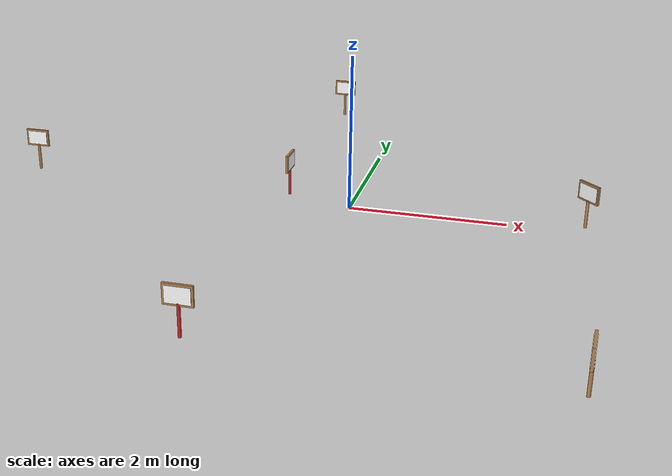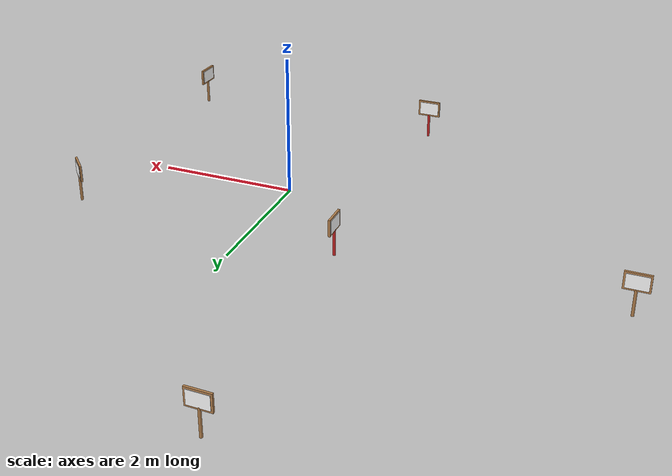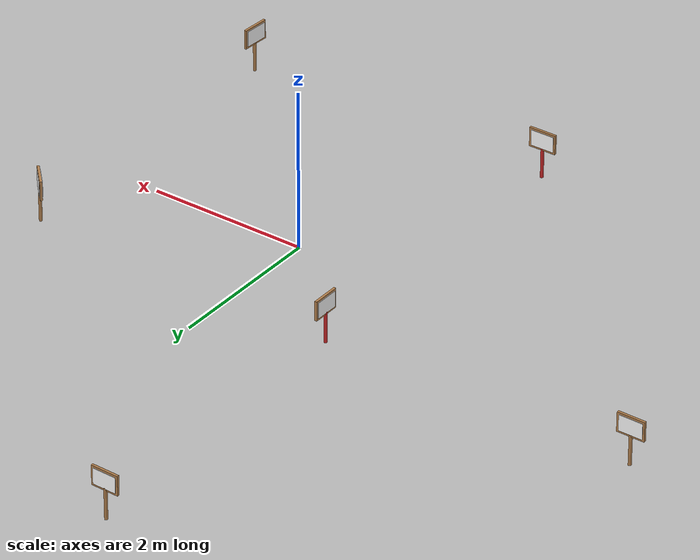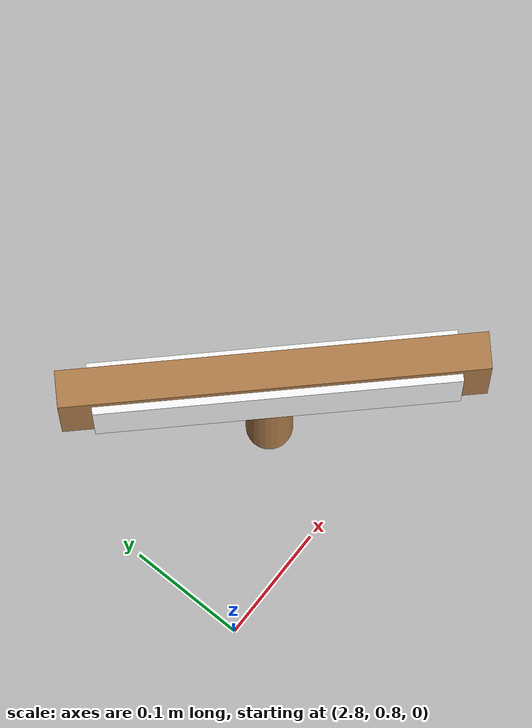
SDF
<?xml version='1.0'?>
<sdf version='1.6'>
  <model name='arrow_maze1'>
    <model name='arrow_wood_thin'>
      <link name='link_0'>
        <inertial>
          <mass>1</mass>
          <inertia>
            <ixx>0.145833</ixx>
            <ixy>0</ixy>
            <ixz>0</ixz>
            <iyy>0.145833</iyy>
            <iyz>0</iyz>
            <izz>0.125</izz>
          </inertia>
          <pose frame=''>0 0 0 0 -0 0</pose>
        </inertial>
        <pose frame=''>-0.017932 0.660168 -0.097628 0 -0 0</pose>
        <gravity>1</gravity>
        <self_collide>0</self_collide>
        <kinematic>0</kinematic>
        <enable_wind>0</enable_wind>
        <visual name='visual'>
          <pose frame=''>0 0 0 0 -0 0</pose>
          <geometry>
            <cylinder>
              <radius>0.02</radius>
              <length>0.4</length>
            </cylinder>
          </geometry>
          <material>
            <lighting>1</lighting>
            <script>
              <uri>file://media/materials/scripts/gazebo.material</uri>
              <name>Gazebo/Wood</name>
            </script>
            <shader type='vertex'>
              <normal_map>__default__</normal_map>
            </shader>
            <ambient>0.3 0.3 0.3 1</ambient>
            <diffuse>0.7 0.7 0.7 1</diffuse>
            <specular>0.01 0.01 0.01 1</specular>
            <emissive>0 0 0 1</emissive>
          </material>
          <transparency>0</transparency>
          <cast_shadows>1</cast_shadows>
        </visual>
        <collision name='collision'>
          <laser_retro>0</laser_retro>
          <max_contacts>10</max_contacts>
          <pose frame=''>0 0 0 0 -0 0</pose>
          <geometry>
            <cylinder>
              <radius>0.02</radius>
              <length>0.4</length>
            </cylinder>
          </geometry>
          <surface>
            <friction>
              <ode>
                <mu>1</mu>
                <mu2>1</mu2>
                <fdir1>0 0 0</fdir1>
                <slip1>0</slip1>
                <slip2>0</slip2>
              </ode>
              <torsional>
                <coefficient>1</coefficient>
                <patch_radius>0</patch_radius>
                <surface_radius>0</surface_radius>
                <use_patch_radius>1</use_patch_radius>
                <ode>
                  <slip>0</slip>
                </ode>
              </torsional>
            </friction>
            <bounce>
              <restitution_coefficient>0</restitution_coefficient>
              <threshold>1e+06</threshold>
            </bounce>
            <contact>
              <collide_without_contact>0</collide_without_contact>
              <collide_without_contact_bitmask>1</collide_without_contact_bitmask>
              <collide_bitmask>1</collide_bitmask>
              <ode>
                <soft_cfm>0</soft_cfm>
                <soft_erp>0.2</soft_erp>
                <kp>1e+13</kp>
                <kd>1</kd>
                <max_vel>0.01</max_vel>
                <min_depth>0</min_depth>
              </ode>
              <bullet>
                <split_impulse>1</split_impulse>
                <split_impulse_penetration_threshold>-0.01</split_impulse_penetration_threshold>
                <soft_cfm>0</soft_cfm>
                <soft_erp>0.2</soft_erp>
                <kp>1e+13</kp>
                <kd>1</kd>
              </bullet>
            </contact>
          </surface>
        </collision>
      </link>
      <link name='link_1'>
        <inertial>
          <mass>2.44097</mass>
          <inertia>
            <ixx>0.0264439</ixx>
            <ixy>0</ixy>
            <ixz>0</ixz>
            <iyy>0.0111671</iyy>
            <iyz>0</iyz>
            <izz>0.0213378</izz>
          </inertia>
          <pose frame=''>0 0 0 0 -0 0</pose>
        </inertial>
        <pose frame=''>-0.025899 0.66382 0.194379 0 -0 0</pose>
        <gravity>1</gravity>
        <self_collide>0</self_collide>
        <kinematic>0</kinematic>
        <enable_wind>0</enable_wind>
        <visual name='visual'>
          <pose frame=''>0 0 0 0 -0 0</pose>
          <geometry>
            <box>
              <size>0.02 0.3 0.2</size>
            </box>
          </geometry>
          <material>
            <script>
              <uri>file://scripts</uri>
              <uri>file://textures</uri>
              <name>arrow/standard</name>
            </script>
            <emissive>0 0 0 1</emissive>
            <shader type='vertex'>
              <normal_map>__default__</normal_map>
            </shader>
            <ambient>1 1 1 1</ambient>
            <diffuse>1 1 1 1</diffuse>
            <specular>0 0 0 1</specular>
          </material>
          <transparency>0</transparency>
          <cast_shadows>1</cast_shadows>
        </visual>
        <collision name='collision'>
          <laser_retro>0</laser_retro>
          <max_contacts>10</max_contacts>
          <pose frame=''>0 0 0 0 -0 0</pose>
          <geometry>
            <box>
              <size>0.02 0.3 0.2</size>
            </box>
          </geometry>
          <surface>
            <friction>
              <ode>
                <mu>1</mu>
                <mu2>1</mu2>
                <fdir1>0 0 0</fdir1>
                <slip1>0</slip1>
                <slip2>0</slip2>
              </ode>
              <torsional>
                <coefficient>1</coefficient>
                <patch_radius>0</patch_radius>
                <surface_radius>0</surface_radius>
                <use_patch_radius>1</use_patch_radius>
                <ode>
                  <slip>0</slip>
                </ode>
              </torsional>
            </friction>
            <bounce>
              <restitution_coefficient>0</restitution_coefficient>
              <threshold>1e+06</threshold>
            </bounce>
            <contact>
              <collide_without_contact>0</collide_without_contact>
              <collide_without_contact_bitmask>1</collide_without_contact_bitmask>
              <collide_bitmask>1</collide_bitmask>
              <ode>
                <soft_cfm>0</soft_cfm>
                <soft_erp>0.2</soft_erp>
                <kp>1e+13</kp>
                <kd>1</kd>
                <max_vel>0.01</max_vel>
                <min_depth>0</min_depth>
              </ode>
              <bullet>
                <split_impulse>1</split_impulse>
                <split_impulse_penetration_threshold>-0.01</split_impulse_penetration_threshold>
                <soft_cfm>0</soft_cfm>
                <soft_erp>0.2</soft_erp>
                <kp>1e+13</kp>
                <kd>1</kd>
              </bullet>
            </contact>
          </surface>
        </collision>
      </link>
      <link name='link_1_clone'>
        <inertial>
          <mass>1</mass>
          <inertia>
            <ixx>0.166667</ixx>
            <ixy>0</ixy>
            <ixz>0</ixz>
            <iyy>0.166667</iyy>
            <iyz>0</iyz>
            <izz>0.166667</izz>
          </inertia>
          <pose frame=''>0 0 0 0 -0 0</pose>
        </inertial>
        <pose frame=''>-0.015207 0.663184 0.195267 0 -0 0</pose>
        <gravity>1</gravity>
        <self_collide>0</self_collide>
        <kinematic>0</kinematic>
        <enable_wind>0</enable_wind>
        <visual name='visual'>
          <pose frame=''>0 0 0 0 -0 0</pose>
          <geometry>
            <box>
              <size>0.03 0.35 0.25</size>
            </box>
          </geometry>
          <material>
            <script>
              <uri>file://scripts</uri>
              <uri>file://textures</uri>
              <name>Gazebo/Wood</name>
            </script>
            <shader type='vertex'>
              <normal_map>__default__</normal_map>
            </shader>
            <ambient>1 1 1 1</ambient>
            <diffuse>1 1 1 1</diffuse>
            <specular>0 0 0 1</specular>
            <emissive>0 0 0 1</emissive>
          </material>
          <transparency>0</transparency>
          <cast_shadows>1</cast_shadows>
        </visual>
        <collision name='collision'>
          <laser_retro>0</laser_retro>
          <max_contacts>10</max_contacts>
          <pose frame=''>0 0 0 0 -0 0</pose>
          <geometry>
            <box>
              <size>0.03 0.35 0.25</size>
            </box>
          </geometry>
          <surface>
            <friction>
              <ode>
                <mu>1</mu>
                <mu2>1</mu2>
                <fdir1>0 0 0</fdir1>
                <slip1>0</slip1>
                <slip2>0</slip2>
              </ode>
              <torsional>
                <coefficient>1</coefficient>
                <patch_radius>0</patch_radius>
                <surface_radius>0</surface_radius>
                <use_patch_radius>1</use_patch_radius>
                <ode>
                  <slip>0</slip>
                </ode>
              </torsional>
            </friction>
            <bounce>
              <restitution_coefficient>0</restitution_coefficient>
              <threshold>1e+06</threshold>
            </bounce>
            <contact>
              <collide_without_contact>0</collide_without_contact>
              <collide_without_contact_bitmask>1</collide_without_contact_bitmask>
              <collide_bitmask>1</collide_bitmask>
              <ode>
                <soft_cfm>0</soft_cfm>
                <soft_erp>0.2</soft_erp>
                <kp>1e+13</kp>
                <kd>1</kd>
                <max_vel>0.01</max_vel>
                <min_depth>0</min_depth>
              </ode>
              <bullet>
                <split_impulse>1</split_impulse>
                <split_impulse_penetration_threshold>-0.01</split_impulse_penetration_threshold>
                <soft_cfm>0</soft_cfm>
                <soft_erp>0.2</soft_erp>
                <kp>1e+13</kp>
                <kd>1</kd>
              </bullet>
            </contact>
          </surface>
        </collision>
      </link>
      <link name='link_1_clone_0'>
        <inertial>
          <mass>0.516012</mass>
          <inertia>
            <ixx>0.00559013</ixx>
            <ixy>0</ixy>
            <ixz>0</ixz>
            <iyy>0.00174866</iyy>
            <iyz>0</iyz>
            <izz>0.00389871</izz>
          </inertia>
          <pose frame=''>0 0 0 0 -0 0</pose>
        </inertial>
        <pose frame=''>-0.00403 0.665261 0.195247 0 -0 0</pose>
        <gravity>1</gravity>
        <self_collide>0</self_collide>
        <kinematic>0</kinematic>
        <enable_wind>0</enable_wind>
        <visual name='visual'>
          <pose frame=''>0 0 0 0 -0 0</pose>
          <geometry>
            <box>
              <size>0.02 0.3 0.2</size>
            </box>
          </geometry>
          <material>
            <script>
              <uri>file://scripts</uri>
              <uri>file://textures</uri>
              <name>arrow/standard_opp</name>
            </script>
            <emissive>0 0 0 1</emissive>
            <shader type='vertex'>
              <normal_map>__default__</normal_map>
            </shader>
            <ambient>1 1 1 1</ambient>
            <diffuse>1 1 1 1</diffuse>
            <specular>0 0 0 1</specular>
          </material>
          <transparency>0</transparency>
          <cast_shadows>1</cast_shadows>
        </visual>
        <collision name='collision'>
          <laser_retro>0</laser_retro>
          <max_contacts>10</max_contacts>
          <pose frame=''>0 0 0 0 -0 0</pose>
          <geometry>
            <box>
              <size>0.02 0.3 0.2</size>
            </box>
          </geometry>
          <surface>
            <friction>
              <ode>
                <mu>1</mu>
                <mu2>1</mu2>
                <fdir1>0 0 0</fdir1>
                <slip1>0</slip1>
                <slip2>0</slip2>
              </ode>
              <torsional>
                <coefficient>1</coefficient>
                <patch_radius>0</patch_radius>
                <surface_radius>0</surface_radius>
                <use_patch_radius>1</use_patch_radius>
                <ode>
                  <slip>0</slip>
                </ode>
              </torsional>
            </friction>
            <bounce>
              <restitution_coefficient>0</restitution_coefficient>
              <threshold>1e+06</threshold>
            </bounce>
            <contact>
              <collide_without_contact>0</collide_without_contact>
              <collide_without_contact_bitmask>1</collide_without_contact_bitmask>
              <collide_bitmask>1</collide_bitmask>
              <ode>
                <soft_cfm>0</soft_cfm>
                <soft_erp>0.2</soft_erp>
                <kp>1e+13</kp>
                <kd>1</kd>
                <max_vel>0.01</max_vel>
                <min_depth>0</min_depth>
              </ode>
              <bullet>
                <split_impulse>1</split_impulse>
                <split_impulse_penetration_threshold>-0.01</split_impulse_penetration_threshold>
                <soft_cfm>0</soft_cfm>
                <soft_erp>0.2</soft_erp>
                <kp>1e+13</kp>
                <kd>1</kd>
              </bullet>
            </contact>
          </surface>
        </collision>
      </link>
      <joint name='link_0_JOINT_0' type='fixed'>
        <parent>link_0</parent>
        <child>link_1</child>
        <pose frame=''>0 0 0 0 -0 0</pose>
        <physics>
          <ode>
            <limit>
              <cfm>0</cfm>
              <erp>0.2</erp>
            </limit>
            <suspension>
              <cfm>0</cfm>
              <erp>0.2</erp>
            </suspension>
          </ode>
        </physics>
      </joint>
      <joint name='link_1_JOINT_0_0' type='fixed'>
        <parent>link_1</parent>
        <child>link_1_clone_0</child>
        <pose frame=''>0 0 0 0 -0 0</pose>
        <physics>
          <ode>
            <limit>
              <cfm>0</cfm>
              <erp>0.2</erp>
            </limit>
            <suspension>
              <cfm>0</cfm>
              <erp>0.2</erp>
            </suspension>
          </ode>
        </physics>
      </joint>
      <joint name='link_1_JOINT_0' type='fixed'>
        <parent>link_1</parent>
        <child>link_1_clone</child>
        <pose frame=''>0 0 0 0 -0 0</pose>
        <physics>
          <ode>
            <limit>
              <cfm>0</cfm>
              <erp>0.2</erp>
            </limit>
            <suspension>
              <cfm>0</cfm>
              <erp>0.2</erp>
            </suspension>
          </ode>
        </physics>
      </joint>
      <static>0</static>
      <allow_auto_disable>1</allow_auto_disable>
      <pose frame=''>-4.38621 0.976128 0 0 -0 1.56944</pose>
    </model>
    <model name='arrow_wood_thin_0'>
      <link name='link_0'>
        <inertial>
          <mass>1</mass>
          <inertia>
            <ixx>0.145833</ixx>
            <ixy>0</ixy>
            <ixz>0</ixz>
            <iyy>0.145833</iyy>
            <iyz>0</iyz>
            <izz>0.125</izz>
          </inertia>
          <pose frame=''>0 0 0 0 -0 0</pose>
        </inertial>
        <pose frame=''>-0.017932 0.660168 -0.097628 0 -0 0</pose>
        <gravity>1</gravity>
        <self_collide>0</self_collide>
        <kinematic>0</kinematic>
        <enable_wind>0</enable_wind>
        <visual name='visual'>
          <pose frame=''>0 0 0 0 -0 0</pose>
          <geometry>
            <cylinder>
              <radius>0.02</radius>
              <length>0.4</length>
            </cylinder>
          </geometry>
          <material>
            <lighting>1</lighting>
            <script>
              <uri>file://media/materials/scripts/gazebo.material</uri>
              <name>Gazebo/Red</name>
            </script>
            <shader type='vertex'>
              <normal_map>__default__</normal_map>
            </shader>
            <ambient>0.3 0.3 0.3 1</ambient>
            <diffuse>0.7 0.7 0.7 1</diffuse>
            <specular>0.01 0.01 0.01 1</specular>
            <emissive>0 0 0 1</emissive>
          </material>
          <transparency>0</transparency>
          <cast_shadows>1</cast_shadows>
        </visual>
        <collision name='collision'>
          <laser_retro>0</laser_retro>
          <max_contacts>10</max_contacts>
          <pose frame=''>0 0 0 0 -0 0</pose>
          <geometry>
            <cylinder>
              <radius>0.02</radius>
              <length>0.4</length>
            </cylinder>
          </geometry>
          <surface>
            <friction>
              <ode>
                <mu>1</mu>
                <mu2>1</mu2>
                <fdir1>0 0 0</fdir1>
                <slip1>0</slip1>
                <slip2>0</slip2>
              </ode>
              <torsional>
                <coefficient>1</coefficient>
                <patch_radius>0</patch_radius>
                <surface_radius>0</surface_radius>
                <use_patch_radius>1</use_patch_radius>
                <ode>
                  <slip>0</slip>
                </ode>
              </torsional>
            </friction>
            <bounce>
              <restitution_coefficient>0</restitution_coefficient>
              <threshold>1e+06</threshold>
            </bounce>
            <contact>
              <collide_without_contact>0</collide_without_contact>
              <collide_without_contact_bitmask>1</collide_without_contact_bitmask>
              <collide_bitmask>1</collide_bitmask>
              <ode>
                <soft_cfm>0</soft_cfm>
                <soft_erp>0.2</soft_erp>
                <kp>1e+13</kp>
                <kd>1</kd>
                <max_vel>0.01</max_vel>
                <min_depth>0</min_depth>
              </ode>
              <bullet>
                <split_impulse>1</split_impulse>
                <split_impulse_penetration_threshold>-0.01</split_impulse_penetration_threshold>
                <soft_cfm>0</soft_cfm>
                <soft_erp>0.2</soft_erp>
                <kp>1e+13</kp>
                <kd>1</kd>
              </bullet>
            </contact>
          </surface>
        </collision>
      </link>
      <link name='link_1'>
        <inertial>
          <mass>2.44097</mass>
          <inertia>
            <ixx>0.0264439</ixx>
            <ixy>0</ixy>
            <ixz>0</ixz>
            <iyy>0.0111671</iyy>
            <iyz>0</iyz>
            <izz>0.0213378</izz>
          </inertia>
          <pose frame=''>0 0 0 0 -0 0</pose>
        </inertial>
        <pose frame=''>-0.025899 0.66382 0.194379 0 -0 0</pose>
        <gravity>1</gravity>
        <self_collide>0</self_collide>
        <kinematic>0</kinematic>
        <enable_wind>0</enable_wind>
        <visual name='visual'>
          <pose frame=''>0 0 0 0 -0 0</pose>
          <geometry>
            <box>
              <size>0.02 0.3 0.2</size>
            </box>
          </geometry>
          <material>
            <script>
              <uri>file://scripts</uri>
              <uri>file://textures</uri>
              <name>arrow/standard</name>
            </script>
            <emissive>0 0 0 1</emissive>
            <shader type='vertex'>
              <normal_map>__default__</normal_map>
            </shader>
            <ambient>1 1 1 1</ambient>
            <diffuse>1 1 1 1</diffuse>
            <specular>0 0 0 1</specular>
          </material>
          <transparency>0</transparency>
          <cast_shadows>1</cast_shadows>
        </visual>
        <collision name='collision'>
          <laser_retro>0</laser_retro>
          <max_contacts>10</max_contacts>
          <pose frame=''>0 0 0 0 -0 0</pose>
          <geometry>
            <box>
              <size>0.02 0.3 0.2</size>
            </box>
          </geometry>
          <surface>
            <friction>
              <ode>
                <mu>1</mu>
                <mu2>1</mu2>
                <fdir1>0 0 0</fdir1>
                <slip1>0</slip1>
                <slip2>0</slip2>
              </ode>
              <torsional>
                <coefficient>1</coefficient>
                <patch_radius>0</patch_radius>
                <surface_radius>0</surface_radius>
                <use_patch_radius>1</use_patch_radius>
                <ode>
                  <slip>0</slip>
                </ode>
              </torsional>
            </friction>
            <bounce>
              <restitution_coefficient>0</restitution_coefficient>
              <threshold>1e+06</threshold>
            </bounce>
            <contact>
              <collide_without_contact>0</collide_without_contact>
              <collide_without_contact_bitmask>1</collide_without_contact_bitmask>
              <collide_bitmask>1</collide_bitmask>
              <ode>
                <soft_cfm>0</soft_cfm>
                <soft_erp>0.2</soft_erp>
                <kp>1e+13</kp>
                <kd>1</kd>
                <max_vel>0.01</max_vel>
                <min_depth>0</min_depth>
              </ode>
              <bullet>
                <split_impulse>1</split_impulse>
                <split_impulse_penetration_threshold>-0.01</split_impulse_penetration_threshold>
                <soft_cfm>0</soft_cfm>
                <soft_erp>0.2</soft_erp>
                <kp>1e+13</kp>
                <kd>1</kd>
              </bullet>
            </contact>
          </surface>
        </collision>
      </link>
      <link name='link_1_clone'>
        <inertial>
          <mass>1</mass>
          <inertia>
            <ixx>0.166667</ixx>
            <ixy>0</ixy>
            <ixz>0</ixz>
            <iyy>0.166667</iyy>
            <iyz>0</iyz>
            <izz>0.166667</izz>
          </inertia>
          <pose frame=''>0 0 0 0 -0 0</pose>
        </inertial>
        <pose frame=''>-0.015207 0.663184 0.195267 0 -0 0</pose>
        <gravity>1</gravity>
        <self_collide>0</self_collide>
        <kinematic>0</kinematic>
        <enable_wind>0</enable_wind>
        <visual name='visual'>
          <pose frame=''>0 0 0 0 -0 0</pose>
          <geometry>
            <box>
              <size>0.03 0.35 0.25</size>
            </box>
          </geometry>
          <material>
            <script>
              <uri>file://scripts</uri>
              <uri>file://textures</uri>
              <name>Gazebo/Wood</name>
            </script>
            <shader type='vertex'>
              <normal_map>__default__</normal_map>
            </shader>
            <ambient>1 1 1 1</ambient>
            <diffuse>1 1 1 1</diffuse>
            <specular>0 0 0 1</specular>
            <emissive>0 0 0 1</emissive>
          </material>
          <transparency>0</transparency>
          <cast_shadows>1</cast_shadows>
        </visual>
        <collision name='collision'>
          <laser_retro>0</laser_retro>
          <max_contacts>10</max_contacts>
          <pose frame=''>0 0 0 0 -0 0</pose>
          <geometry>
            <box>
              <size>0.03 0.35 0.25</size>
            </box>
          </geometry>
          <surface>
            <friction>
              <ode>
                <mu>1</mu>
                <mu2>1</mu2>
                <fdir1>0 0 0</fdir1>
                <slip1>0</slip1>
                <slip2>0</slip2>
              </ode>
              <torsional>
                <coefficient>1</coefficient>
                <patch_radius>0</patch_radius>
                <surface_radius>0</surface_radius>
                <use_patch_radius>1</use_patch_radius>
                <ode>
                  <slip>0</slip>
                </ode>
              </torsional>
            </friction>
            <bounce>
              <restitution_coefficient>0</restitution_coefficient>
              <threshold>1e+06</threshold>
            </bounce>
            <contact>
              <collide_without_contact>0</collide_without_contact>
              <collide_without_contact_bitmask>1</collide_without_contact_bitmask>
              <collide_bitmask>1</collide_bitmask>
              <ode>
                <soft_cfm>0</soft_cfm>
                <soft_erp>0.2</soft_erp>
                <kp>1e+13</kp>
                <kd>1</kd>
                <max_vel>0.01</max_vel>
                <min_depth>0</min_depth>
              </ode>
              <bullet>
                <split_impulse>1</split_impulse>
                <split_impulse_penetration_threshold>-0.01</split_impulse_penetration_threshold>
                <soft_cfm>0</soft_cfm>
                <soft_erp>0.2</soft_erp>
                <kp>1e+13</kp>
                <kd>1</kd>
              </bullet>
            </contact>
          </surface>
        </collision>
      </link>
      <link name='link_1_clone_0'>
        <inertial>
          <mass>0.516012</mass>
          <inertia>
            <ixx>0.00559013</ixx>
            <ixy>0</ixy>
            <ixz>0</ixz>
            <iyy>0.00174866</iyy>
            <iyz>0</iyz>
            <izz>0.00389871</izz>
          </inertia>
          <pose frame=''>0 0 0 0 -0 0</pose>
        </inertial>
        <pose frame=''>-0.00403 0.665261 0.195247 0 -0 0</pose>
        <gravity>1</gravity>
        <self_collide>0</self_collide>
        <kinematic>0</kinematic>
        <enable_wind>0</enable_wind>
        <visual name='visual'>
          <pose frame=''>0 0 0 0 -0 0</pose>
          <geometry>
            <box>
              <size>0.02 0.3 0.2</size>
            </box>
          </geometry>
          <material>
            <script>
              <uri>file://scripts</uri>
              <uri>file://textures</uri>
              <name>arrow/standard_opp</name>
            </script>
            <emissive>0 0 0 1</emissive>
            <shader type='vertex'>
              <normal_map>__default__</normal_map>
            </shader>
            <ambient>1 1 1 1</ambient>
            <diffuse>1 1 1 1</diffuse>
            <specular>0 0 0 1</specular>
          </material>
          <transparency>0</transparency>
          <cast_shadows>1</cast_shadows>
        </visual>
        <collision name='collision'>
          <laser_retro>0</laser_retro>
          <max_contacts>10</max_contacts>
          <pose frame=''>0 0 0 0 -0 0</pose>
          <geometry>
            <box>
              <size>0.02 0.3 0.2</size>
            </box>
          </geometry>
          <surface>
            <friction>
              <ode>
                <mu>1</mu>
                <mu2>1</mu2>
                <fdir1>0 0 0</fdir1>
                <slip1>0</slip1>
                <slip2>0</slip2>
              </ode>
              <torsional>
                <coefficient>1</coefficient>
                <patch_radius>0</patch_radius>
                <surface_radius>0</surface_radius>
                <use_patch_radius>1</use_patch_radius>
                <ode>
                  <slip>0</slip>
                </ode>
              </torsional>
            </friction>
            <bounce>
              <restitution_coefficient>0</restitution_coefficient>
              <threshold>1e+06</threshold>
            </bounce>
            <contact>
              <collide_without_contact>0</collide_without_contact>
              <collide_without_contact_bitmask>1</collide_without_contact_bitmask>
              <collide_bitmask>1</collide_bitmask>
              <ode>
                <soft_cfm>0</soft_cfm>
                <soft_erp>0.2</soft_erp>
                <kp>1e+13</kp>
                <kd>1</kd>
                <max_vel>0.01</max_vel>
                <min_depth>0</min_depth>
              </ode>
              <bullet>
                <split_impulse>1</split_impulse>
                <split_impulse_penetration_threshold>-0.01</split_impulse_penetration_threshold>
                <soft_cfm>0</soft_cfm>
                <soft_erp>0.2</soft_erp>
                <kp>1e+13</kp>
                <kd>1</kd>
              </bullet>
            </contact>
          </surface>
        </collision>
      </link>
      <joint name='link_0_JOINT_0' type='fixed'>
        <parent>link_0</parent>
        <child>link_1</child>
        <pose frame=''>0 0 0 0 -0 0</pose>
        <physics>
          <ode>
            <limit>
              <cfm>0</cfm>
              <erp>0.2</erp>
            </limit>
            <suspension>
              <cfm>0</cfm>
              <erp>0.2</erp>
            </suspension>
          </ode>
        </physics>
      </joint>
      <joint name='link_1_JOINT_0_0' type='fixed'>
        <parent>link_1</parent>
        <child>link_1_clone_0</child>
        <pose frame=''>0 0 0 0 -0 0</pose>
        <physics>
          <ode>
            <limit>
              <cfm>0</cfm>
              <erp>0.2</erp>
            </limit>
            <suspension>
              <cfm>0</cfm>
              <erp>0.2</erp>
            </suspension>
          </ode>
        </physics>
      </joint>
      <joint name='link_1_JOINT_0' type='fixed'>
        <parent>link_1</parent>
        <child>link_1_clone</child>
        <pose frame=''>0 0 0 0 -0 0</pose>
        <physics>
          <ode>
            <limit>
              <cfm>0</cfm>
              <erp>0.2</erp>
            </limit>
            <suspension>
              <cfm>0</cfm>
              <erp>0.2</erp>
            </suspension>
          </ode>
        </physics>
      </joint>
      <static>0</static>
      <allow_auto_disable>1</allow_auto_disable>
      <pose frame=''>-1.0729 0.322933 -0 0 -0 0</pose>
    </model>
    <model name='arrow_wood_thin_1'>
      <link name='link_0'>
        <inertial>
          <mass>1</mass>
          <inertia>
            <ixx>0.145833</ixx>
            <ixy>0</ixy>
            <ixz>0</ixz>
            <iyy>0.145833</iyy>
            <iyz>0</iyz>
            <izz>0.125</izz>
          </inertia>
          <pose frame=''>0 0 0 0 -0 0</pose>
        </inertial>
        <pose frame=''>-0.017932 0.660168 -0.097628 0 -0 0</pose>
        <gravity>1</gravity>
        <self_collide>0</self_collide>
        <kinematic>0</kinematic>
        <enable_wind>0</enable_wind>
        <visual name='visual'>
          <pose frame=''>0 0 0 0 -0 0</pose>
          <geometry>
            <cylinder>
              <radius>0.02</radius>
              <length>0.4</length>
            </cylinder>
          </geometry>
          <material>
            <lighting>1</lighting>
            <script>
              <uri>file://media/materials/scripts/gazebo.material</uri>
              <name>Gazebo/Red</name>
            </script>
            <shader type='vertex'>
              <normal_map>__default__</normal_map>
            </shader>
            <ambient>0.3 0.3 0.3 1</ambient>
            <diffuse>0.7 0.7 0.7 1</diffuse>
            <specular>0.01 0.01 0.01 1</specular>
            <emissive>0 0 0 1</emissive>
          </material>
          <transparency>0</transparency>
          <cast_shadows>1</cast_shadows>
        </visual>
        <collision name='collision'>
          <laser_retro>0</laser_retro>
          <max_contacts>10</max_contacts>
          <pose frame=''>0 0 0 0 -0 0</pose>
          <geometry>
            <cylinder>
              <radius>0.02</radius>
              <length>0.4</length>
            </cylinder>
          </geometry>
          <surface>
            <friction>
              <ode>
                <mu>1</mu>
                <mu2>1</mu2>
                <fdir1>0 0 0</fdir1>
                <slip1>0</slip1>
                <slip2>0</slip2>
              </ode>
              <torsional>
                <coefficient>1</coefficient>
                <patch_radius>0</patch_radius>
                <surface_radius>0</surface_radius>
                <use_patch_radius>1</use_patch_radius>
                <ode>
                  <slip>0</slip>
                </ode>
              </torsional>
            </friction>
            <bounce>
              <restitution_coefficient>0</restitution_coefficient>
              <threshold>1e+06</threshold>
            </bounce>
            <contact>
              <collide_without_contact>0</collide_without_contact>
              <collide_without_contact_bitmask>1</collide_without_contact_bitmask>
              <collide_bitmask>1</collide_bitmask>
              <ode>
                <soft_cfm>0</soft_cfm>
                <soft_erp>0.2</soft_erp>
                <kp>1e+13</kp>
                <kd>1</kd>
                <max_vel>0.01</max_vel>
                <min_depth>0</min_depth>
              </ode>
              <bullet>
                <split_impulse>1</split_impulse>
                <split_impulse_penetration_threshold>-0.01</split_impulse_penetration_threshold>
                <soft_cfm>0</soft_cfm>
                <soft_erp>0.2</soft_erp>
                <kp>1e+13</kp>
                <kd>1</kd>
              </bullet>
            </contact>
          </surface>
        </collision>
      </link>
      <link name='link_1'>
        <inertial>
          <mass>2.44097</mass>
          <inertia>
            <ixx>0.0264439</ixx>
            <ixy>0</ixy>
            <ixz>0</ixz>
            <iyy>0.0111671</iyy>
            <iyz>0</iyz>
            <izz>0.0213378</izz>
          </inertia>
          <pose frame=''>0 0 0 0 -0 0</pose>
        </inertial>
        <pose frame=''>-0.025899 0.66382 0.194379 0 -0 0</pose>
        <gravity>1</gravity>
        <self_collide>0</self_collide>
        <kinematic>0</kinematic>
        <enable_wind>0</enable_wind>
        <visual name='visual'>
          <pose frame=''>0 0 0 0 -0 0</pose>
          <geometry>
            <box>
              <size>0.02 0.3 0.2</size>
            </box>
          </geometry>
          <material>
            <script>
              <uri>file://scripts</uri>
              <uri>file://textures</uri>
              <name>arrow/standard</name>
            </script>
            <emissive>0 0 0 1</emissive>
            <shader type='vertex'>
              <normal_map>__default__</normal_map>
            </shader>
            <ambient>1 1 1 1</ambient>
            <diffuse>1 1 1 1</diffuse>
            <specular>0 0 0 1</specular>
          </material>
          <transparency>0</transparency>
          <cast_shadows>1</cast_shadows>
        </visual>
        <collision name='collision'>
          <laser_retro>0</laser_retro>
          <max_contacts>10</max_contacts>
          <pose frame=''>0 0 0 0 -0 0</pose>
          <geometry>
            <box>
              <size>0.02 0.3 0.2</size>
            </box>
          </geometry>
          <surface>
            <friction>
              <ode>
                <mu>1</mu>
                <mu2>1</mu2>
                <fdir1>0 0 0</fdir1>
                <slip1>0</slip1>
                <slip2>0</slip2>
              </ode>
              <torsional>
                <coefficient>1</coefficient>
                <patch_radius>0</patch_radius>
                <surface_radius>0</surface_radius>
                <use_patch_radius>1</use_patch_radius>
                <ode>
                  <slip>0</slip>
                </ode>
              </torsional>
            </friction>
            <bounce>
              <restitution_coefficient>0</restitution_coefficient>
              <threshold>1e+06</threshold>
            </bounce>
            <contact>
              <collide_without_contact>0</collide_without_contact>
              <collide_without_contact_bitmask>1</collide_without_contact_bitmask>
              <collide_bitmask>1</collide_bitmask>
              <ode>
                <soft_cfm>0</soft_cfm>
                <soft_erp>0.2</soft_erp>
                <kp>1e+13</kp>
                <kd>1</kd>
                <max_vel>0.01</max_vel>
                <min_depth>0</min_depth>
              </ode>
              <bullet>
                <split_impulse>1</split_impulse>
                <split_impulse_penetration_threshold>-0.01</split_impulse_penetration_threshold>
                <soft_cfm>0</soft_cfm>
                <soft_erp>0.2</soft_erp>
                <kp>1e+13</kp>
                <kd>1</kd>
              </bullet>
            </contact>
          </surface>
        </collision>
      </link>
      <link name='link_1_clone'>
        <inertial>
          <mass>1</mass>
          <inertia>
            <ixx>0.166667</ixx>
            <ixy>0</ixy>
            <ixz>0</ixz>
            <iyy>0.166667</iyy>
            <iyz>0</iyz>
            <izz>0.166667</izz>
          </inertia>
          <pose frame=''>0 0 0 0 -0 0</pose>
        </inertial>
        <pose frame=''>-0.015207 0.663184 0.195267 0 -0 0</pose>
        <gravity>1</gravity>
        <self_collide>0</self_collide>
        <kinematic>0</kinematic>
        <enable_wind>0</enable_wind>
        <visual name='visual'>
          <pose frame=''>0 0 0 0 -0 0</pose>
          <geometry>
            <box>
              <size>0.03 0.35 0.25</size>
            </box>
          </geometry>
          <material>
            <script>
              <uri>file://scripts</uri>
              <uri>file://textures</uri>
              <name>Gazebo/Wood</name>
            </script>
            <shader type='vertex'>
              <normal_map>__default__</normal_map>
            </shader>
            <ambient>1 1 1 1</ambient>
            <diffuse>1 1 1 1</diffuse>
            <specular>0 0 0 1</specular>
            <emissive>0 0 0 1</emissive>
          </material>
          <transparency>0</transparency>
          <cast_shadows>1</cast_shadows>
        </visual>
        <collision name='collision'>
          <laser_retro>0</laser_retro>
          <max_contacts>10</max_contacts>
          <pose frame=''>0 0 0 0 -0 0</pose>
          <geometry>
            <box>
              <size>0.03 0.35 0.25</size>
            </box>
          </geometry>
          <surface>
            <friction>
              <ode>
                <mu>1</mu>
                <mu2>1</mu2>
                <fdir1>0 0 0</fdir1>
                <slip1>0</slip1>
                <slip2>0</slip2>
              </ode>
              <torsional>
                <coefficient>1</coefficient>
                <patch_radius>0</patch_radius>
                <surface_radius>0</surface_radius>
                <use_patch_radius>1</use_patch_radius>
                <ode>
                  <slip>0</slip>
                </ode>
              </torsional>
            </friction>
            <bounce>
              <restitution_coefficient>0</restitution_coefficient>
              <threshold>1e+06</threshold>
            </bounce>
            <contact>
              <collide_without_contact>0</collide_without_contact>
              <collide_without_contact_bitmask>1</collide_without_contact_bitmask>
              <collide_bitmask>1</collide_bitmask>
              <ode>
                <soft_cfm>0</soft_cfm>
                <soft_erp>0.2</soft_erp>
                <kp>1e+13</kp>
                <kd>1</kd>
                <max_vel>0.01</max_vel>
                <min_depth>0</min_depth>
              </ode>
              <bullet>
                <split_impulse>1</split_impulse>
                <split_impulse_penetration_threshold>-0.01</split_impulse_penetration_threshold>
                <soft_cfm>0</soft_cfm>
                <soft_erp>0.2</soft_erp>
                <kp>1e+13</kp>
                <kd>1</kd>
              </bullet>
            </contact>
          </surface>
        </collision>
      </link>
      <link name='link_1_clone_0'>
        <inertial>
          <mass>0.516012</mass>
          <inertia>
            <ixx>0.00559013</ixx>
            <ixy>0</ixy>
            <ixz>0</ixz>
            <iyy>0.00174866</iyy>
            <iyz>0</iyz>
            <izz>0.00389871</izz>
          </inertia>
          <pose frame=''>0 0 0 0 -0 0</pose>
        </inertial>
        <pose frame=''>-0.00403 0.665261 0.195247 0 -0 0</pose>
        <gravity>1</gravity>
        <self_collide>0</self_collide>
        <kinematic>0</kinematic>
        <enable_wind>0</enable_wind>
        <visual name='visual'>
          <pose frame=''>0 0 0 0 -0 0</pose>
          <geometry>
            <box>
              <size>0.02 0.3 0.2</size>
            </box>
          </geometry>
          <material>
            <script>
              <uri>file://scripts</uri>
              <uri>file://textures</uri>
              <name>arrow/standard_opp</name>
            </script>
            <emissive>0 0 0 1</emissive>
            <shader type='vertex'>
              <normal_map>__default__</normal_map>
            </shader>
            <ambient>1 1 1 1</ambient>
            <diffuse>1 1 1 1</diffuse>
            <specular>0 0 0 1</specular>
          </material>
          <transparency>0</transparency>
          <cast_shadows>1</cast_shadows>
        </visual>
        <collision name='collision'>
          <laser_retro>0</laser_retro>
          <max_contacts>10</max_contacts>
          <pose frame=''>0 0 0 0 -0 0</pose>
          <geometry>
            <box>
              <size>0.02 0.3 0.2</size>
            </box>
          </geometry>
          <surface>
            <friction>
              <ode>
                <mu>1</mu>
                <mu2>1</mu2>
                <fdir1>0 0 0</fdir1>
                <slip1>0</slip1>
                <slip2>0</slip2>
              </ode>
              <torsional>
                <coefficient>1</coefficient>
                <patch_radius>0</patch_radius>
                <surface_radius>0</surface_radius>
                <use_patch_radius>1</use_patch_radius>
                <ode>
                  <slip>0</slip>
                </ode>
              </torsional>
            </friction>
            <bounce>
              <restitution_coefficient>0</restitution_coefficient>
              <threshold>1e+06</threshold>
            </bounce>
            <contact>
              <collide_without_contact>0</collide_without_contact>
              <collide_without_contact_bitmask>1</collide_without_contact_bitmask>
              <collide_bitmask>1</collide_bitmask>
              <ode>
                <soft_cfm>0</soft_cfm>
                <soft_erp>0.2</soft_erp>
                <kp>1e+13</kp>
                <kd>1</kd>
                <max_vel>0.01</max_vel>
                <min_depth>0</min_depth>
              </ode>
              <bullet>
                <split_impulse>1</split_impulse>
                <split_impulse_penetration_threshold>-0.01</split_impulse_penetration_threshold>
                <soft_cfm>0</soft_cfm>
                <soft_erp>0.2</soft_erp>
                <kp>1e+13</kp>
                <kd>1</kd>
              </bullet>
            </contact>
          </surface>
        </collision>
      </link>
      <joint name='link_0_JOINT_0' type='fixed'>
        <parent>link_0</parent>
        <child>link_1</child>
        <pose frame=''>0 0 0 0 -0 0</pose>
        <physics>
          <ode>
            <limit>
              <cfm>0</cfm>
              <erp>0.2</erp>
            </limit>
            <suspension>
              <cfm>0</cfm>
              <erp>0.2</erp>
            </suspension>
          </ode>
        </physics>
      </joint>
      <joint name='link_1_JOINT_0_0' type='fixed'>
        <parent>link_1</parent>
        <child>link_1_clone_0</child>
        <pose frame=''>0 0 0 0 -0 0</pose>
        <physics>
          <ode>
            <limit>
              <cfm>0</cfm>
              <erp>0.2</erp>
            </limit>
            <suspension>
              <cfm>0</cfm>
              <erp>0.2</erp>
            </suspension>
          </ode>
        </physics>
      </joint>
      <joint name='link_1_JOINT_0' type='fixed'>
        <parent>link_1</parent>
        <child>link_1_clone</child>
        <pose frame=''>0 0 0 0 -0 0</pose>
        <physics>
          <ode>
            <limit>
              <cfm>0</cfm>
              <erp>0.2</erp>
            </limit>
            <suspension>
              <cfm>0</cfm>
              <erp>0.2</erp>
            </suspension>
          </ode>
        </physics>
      </joint>
      <static>0</static>
      <allow_auto_disable>1</allow_auto_disable>
      <pose frame=''>-0.398383 -3.20124 0 0 0 1.58196</pose>
    </model>
    <model name='arrow_wood_thin_2'>
      <link name='link_0'>
        <inertial>
          <mass>1</mass>
          <inertia>
            <ixx>0.145833</ixx>
            <ixy>0</ixy>
            <ixz>0</ixz>
            <iyy>0.145833</iyy>
            <iyz>0</iyz>
            <izz>0.125</izz>
          </inertia>
          <pose frame=''>0 0 0 0 -0 0</pose>
        </inertial>
        <pose frame=''>-0.017932 0.660168 -0.097628 0 -0 0</pose>
        <gravity>1</gravity>
        <self_collide>0</self_collide>
        <kinematic>0</kinematic>
        <enable_wind>0</enable_wind>
        <visual name='visual'>
          <pose frame=''>0 0 0 0 -0 0</pose>
          <geometry>
            <cylinder>
              <radius>0.02</radius>
              <length>0.4</length>
            </cylinder>
          </geometry>
          <material>
            <lighting>1</lighting>
            <script>
              <uri>file://media/materials/scripts/gazebo.material</uri>
              <name>Gazebo/Wood</name>
            </script>
            <shader type='vertex'>
              <normal_map>__default__</normal_map>
            </shader>
            <ambient>0.3 0.3 0.3 1</ambient>
            <diffuse>0.7 0.7 0.7 1</diffuse>
            <specular>0.01 0.01 0.01 1</specular>
            <emissive>0 0 0 1</emissive>
          </material>
          <transparency>0</transparency>
          <cast_shadows>1</cast_shadows>
        </visual>
        <collision name='collision'>
          <laser_retro>0</laser_retro>
          <max_contacts>10</max_contacts>
          <pose frame=''>0 0 0 0 -0 0</pose>
          <geometry>
            <cylinder>
              <radius>0.02</radius>
              <length>0.4</length>
            </cylinder>
          </geometry>
          <surface>
            <friction>
              <ode>
                <mu>1</mu>
                <mu2>1</mu2>
                <fdir1>0 0 0</fdir1>
                <slip1>0</slip1>
                <slip2>0</slip2>
              </ode>
              <torsional>
                <coefficient>1</coefficient>
                <patch_radius>0</patch_radius>
                <surface_radius>0</surface_radius>
                <use_patch_radius>1</use_patch_radius>
                <ode>
                  <slip>0</slip>
                </ode>
              </torsional>
            </friction>
            <bounce>
              <restitution_coefficient>0</restitution_coefficient>
              <threshold>1e+06</threshold>
            </bounce>
            <contact>
              <collide_without_contact>0</collide_without_contact>
              <collide_without_contact_bitmask>1</collide_without_contact_bitmask>
              <collide_bitmask>1</collide_bitmask>
              <ode>
                <soft_cfm>0</soft_cfm>
                <soft_erp>0.2</soft_erp>
                <kp>1e+13</kp>
                <kd>1</kd>
                <max_vel>0.01</max_vel>
                <min_depth>0</min_depth>
              </ode>
              <bullet>
                <split_impulse>1</split_impulse>
                <split_impulse_penetration_threshold>-0.01</split_impulse_penetration_threshold>
                <soft_cfm>0</soft_cfm>
                <soft_erp>0.2</soft_erp>
                <kp>1e+13</kp>
                <kd>1</kd>
              </bullet>
            </contact>
          </surface>
        </collision>
      </link>
      <link name='link_1'>
        <inertial>
          <mass>2.44097</mass>
          <inertia>
            <ixx>0.0264439</ixx>
            <ixy>0</ixy>
            <ixz>0</ixz>
            <iyy>0.0111671</iyy>
            <iyz>0</iyz>
            <izz>0.0213378</izz>
          </inertia>
          <pose frame=''>0 0 0 0 -0 0</pose>
        </inertial>
        <pose frame=''>-0.025899 0.66382 0.194379 0 -0 0</pose>
        <gravity>1</gravity>
        <self_collide>0</self_collide>
        <kinematic>0</kinematic>
        <enable_wind>0</enable_wind>
        <visual name='visual'>
          <pose frame=''>0 0 0 0 -0 0</pose>
          <geometry>
            <box>
              <size>0.02 0.3 0.2</size>
            </box>
          </geometry>
          <material>
            <script>
              <uri>file://scripts</uri>
              <uri>file://textures</uri>
              <name>arrow/standard</name>
            </script>
            <emissive>0 0 0 1</emissive>
            <shader type='vertex'>
              <normal_map>__default__</normal_map>
            </shader>
            <ambient>1 1 1 1</ambient>
            <diffuse>1 1 1 1</diffuse>
            <specular>0 0 0 1</specular>
          </material>
          <transparency>0</transparency>
          <cast_shadows>1</cast_shadows>
        </visual>
        <collision name='collision'>
          <laser_retro>0</laser_retro>
          <max_contacts>10</max_contacts>
          <pose frame=''>0 0 0 0 -0 0</pose>
          <geometry>
            <box>
              <size>0.02 0.3 0.2</size>
            </box>
          </geometry>
          <surface>
            <friction>
              <ode>
                <mu>1</mu>
                <mu2>1</mu2>
                <fdir1>0 0 0</fdir1>
                <slip1>0</slip1>
                <slip2>0</slip2>
              </ode>
              <torsional>
                <coefficient>1</coefficient>
                <patch_radius>0</patch_radius>
                <surface_radius>0</surface_radius>
                <use_patch_radius>1</use_patch_radius>
                <ode>
                  <slip>0</slip>
                </ode>
              </torsional>
            </friction>
            <bounce>
              <restitution_coefficient>0</restitution_coefficient>
              <threshold>1e+06</threshold>
            </bounce>
            <contact>
              <collide_without_contact>0</collide_without_contact>
              <collide_without_contact_bitmask>1</collide_without_contact_bitmask>
              <collide_bitmask>1</collide_bitmask>
              <ode>
                <soft_cfm>0</soft_cfm>
                <soft_erp>0.2</soft_erp>
                <kp>1e+13</kp>
                <kd>1</kd>
                <max_vel>0.01</max_vel>
                <min_depth>0</min_depth>
              </ode>
              <bullet>
                <split_impulse>1</split_impulse>
                <split_impulse_penetration_threshold>-0.01</split_impulse_penetration_threshold>
                <soft_cfm>0</soft_cfm>
                <soft_erp>0.2</soft_erp>
                <kp>1e+13</kp>
                <kd>1</kd>
              </bullet>
            </contact>
          </surface>
        </collision>
      </link>
      <link name='link_1_clone'>
        <inertial>
          <mass>1</mass>
          <inertia>
            <ixx>0.166667</ixx>
            <ixy>0</ixy>
            <ixz>0</ixz>
            <iyy>0.166667</iyy>
            <iyz>0</iyz>
            <izz>0.166667</izz>
          </inertia>
          <pose frame=''>0 0 0 0 -0 0</pose>
        </inertial>
        <pose frame=''>-0.015207 0.663184 0.195267 0 -0 0</pose>
        <gravity>1</gravity>
        <self_collide>0</self_collide>
        <kinematic>0</kinematic>
        <enable_wind>0</enable_wind>
        <visual name='visual'>
          <pose frame=''>0 0 0 0 -0 0</pose>
          <geometry>
            <box>
              <size>0.03 0.35 0.25</size>
            </box>
          </geometry>
          <material>
            <script>
              <uri>file://scripts</uri>
              <uri>file://textures</uri>
              <name>Gazebo/Wood</name>
            </script>
            <shader type='vertex'>
              <normal_map>__default__</normal_map>
            </shader>
            <ambient>1 1 1 1</ambient>
            <diffuse>1 1 1 1</diffuse>
            <specular>0 0 0 1</specular>
            <emissive>0 0 0 1</emissive>
          </material>
          <transparency>0</transparency>
          <cast_shadows>1</cast_shadows>
        </visual>
        <collision name='collision'>
          <laser_retro>0</laser_retro>
          <max_contacts>10</max_contacts>
          <pose frame=''>0 0 0 0 -0 0</pose>
          <geometry>
            <box>
              <size>0.03 0.35 0.25</size>
            </box>
          </geometry>
          <surface>
            <friction>
              <ode>
                <mu>1</mu>
                <mu2>1</mu2>
                <fdir1>0 0 0</fdir1>
                <slip1>0</slip1>
                <slip2>0</slip2>
              </ode>
              <torsional>
                <coefficient>1</coefficient>
                <patch_radius>0</patch_radius>
                <surface_radius>0</surface_radius>
                <use_patch_radius>1</use_patch_radius>
                <ode>
                  <slip>0</slip>
                </ode>
              </torsional>
            </friction>
            <bounce>
              <restitution_coefficient>0</restitution_coefficient>
              <threshold>1e+06</threshold>
            </bounce>
            <contact>
              <collide_without_contact>0</collide_without_contact>
              <collide_without_contact_bitmask>1</collide_without_contact_bitmask>
              <collide_bitmask>1</collide_bitmask>
              <ode>
                <soft_cfm>0</soft_cfm>
                <soft_erp>0.2</soft_erp>
                <kp>1e+13</kp>
                <kd>1</kd>
                <max_vel>0.01</max_vel>
                <min_depth>0</min_depth>
              </ode>
              <bullet>
                <split_impulse>1</split_impulse>
                <split_impulse_penetration_threshold>-0.01</split_impulse_penetration_threshold>
                <soft_cfm>0</soft_cfm>
                <soft_erp>0.2</soft_erp>
                <kp>1e+13</kp>
                <kd>1</kd>
              </bullet>
            </contact>
          </surface>
        </collision>
      </link>
      <link name='link_1_clone_0'>
        <inertial>
          <mass>0.516012</mass>
          <inertia>
            <ixx>0.00559013</ixx>
            <ixy>0</ixy>
            <ixz>0</ixz>
            <iyy>0.00174866</iyy>
            <iyz>0</iyz>
            <izz>0.00389871</izz>
          </inertia>
          <pose frame=''>0 0 0 0 -0 0</pose>
        </inertial>
        <pose frame=''>-0.00403 0.665261 0.195247 0 -0 0</pose>
        <gravity>1</gravity>
        <self_collide>0</self_collide>
        <kinematic>0</kinematic>
        <enable_wind>0</enable_wind>
        <visual name='visual'>
          <pose frame=''>0 0 0 0 -0 0</pose>
          <geometry>
            <box>
              <size>0.02 0.3 0.2</size>
            </box>
          </geometry>
          <material>
            <script>
              <uri>file://scripts</uri>
              <uri>file://textures</uri>
              <name>arrow/standard_opp</name>
            </script>
            <emissive>0 0 0 1</emissive>
            <shader type='vertex'>
              <normal_map>__default__</normal_map>
            </shader>
            <ambient>1 1 1 1</ambient>
            <diffuse>1 1 1 1</diffuse>
            <specular>0 0 0 1</specular>
          </material>
          <transparency>0</transparency>
          <cast_shadows>1</cast_shadows>
        </visual>
        <collision name='collision'>
          <laser_retro>0</laser_retro>
          <max_contacts>10</max_contacts>
          <pose frame=''>0 0 0 0 -0 0</pose>
          <geometry>
            <box>
              <size>0.02 0.3 0.2</size>
            </box>
          </geometry>
          <surface>
            <friction>
              <ode>
                <mu>1</mu>
                <mu2>1</mu2>
                <fdir1>0 0 0</fdir1>
                <slip1>0</slip1>
                <slip2>0</slip2>
              </ode>
              <torsional>
                <coefficient>1</coefficient>
                <patch_radius>0</patch_radius>
                <surface_radius>0</surface_radius>
                <use_patch_radius>1</use_patch_radius>
                <ode>
                  <slip>0</slip>
                </ode>
              </torsional>
            </friction>
            <bounce>
              <restitution_coefficient>0</restitution_coefficient>
              <threshold>1e+06</threshold>
            </bounce>
            <contact>
              <collide_without_contact>0</collide_without_contact>
              <collide_without_contact_bitmask>1</collide_without_contact_bitmask>
              <collide_bitmask>1</collide_bitmask>
              <ode>
                <soft_cfm>0</soft_cfm>
                <soft_erp>0.2</soft_erp>
                <kp>1e+13</kp>
                <kd>1</kd>
                <max_vel>0.01</max_vel>
                <min_depth>0</min_depth>
              </ode>
              <bullet>
                <split_impulse>1</split_impulse>
                <split_impulse_penetration_threshold>-0.01</split_impulse_penetration_threshold>
                <soft_cfm>0</soft_cfm>
                <soft_erp>0.2</soft_erp>
                <kp>1e+13</kp>
                <kd>1</kd>
              </bullet>
            </contact>
          </surface>
        </collision>
      </link>
      <joint name='link_0_JOINT_0' type='fixed'>
        <parent>link_0</parent>
        <child>link_1</child>
        <pose frame=''>0 0 0 0 -0 0</pose>
        <physics>
          <ode>
            <limit>
              <cfm>0</cfm>
              <erp>0.2</erp>
            </limit>
            <suspension>
              <cfm>0</cfm>
              <erp>0.2</erp>
            </suspension>
          </ode>
        </physics>
      </joint>
      <joint name='link_1_JOINT_0_0' type='fixed'>
        <parent>link_1</parent>
        <child>link_1_clone_0</child>
        <pose frame=''>0 0 0 0 -0 0</pose>
        <physics>
          <ode>
            <limit>
              <cfm>0</cfm>
              <erp>0.2</erp>
            </limit>
            <suspension>
              <cfm>0</cfm>
              <erp>0.2</erp>
            </suspension>
          </ode>
        </physics>
      </joint>
      <joint name='link_1_JOINT_0' type='fixed'>
        <parent>link_1</parent>
        <child>link_1_clone</child>
        <pose frame=''>0 0 0 0 -0 0</pose>
        <physics>
          <ode>
            <limit>
              <cfm>0</cfm>
              <erp>0.2</erp>
            </limit>
            <suspension>
              <cfm>0</cfm>
              <erp>0.2</erp>
            </suspension>
          </ode>
        </physics>
      </joint>
      <static>0</static>
      <allow_auto_disable>1</allow_auto_disable>
      <pose frame=''>3.04989 -2.53018 -0 0 -0 3.07868</pose>
    </model>
    <model name='arrow_wood_thin_3'>
      <link name='link_0'>
        <inertial>
          <mass>1</mass>
          <inertia>
            <ixx>0.145833</ixx>
            <ixy>0</ixy>
            <ixz>0</ixz>
            <iyy>0.145833</iyy>
            <iyz>0</iyz>
            <izz>0.125</izz>
          </inertia>
          <pose frame=''>0 0 0 0 -0 0</pose>
        </inertial>
        <pose frame=''>-0.017932 0.660168 -0.097628 0 -0 0</pose>
        <gravity>1</gravity>
        <self_collide>0</self_collide>
        <kinematic>0</kinematic>
        <enable_wind>0</enable_wind>
        <visual name='visual'>
          <pose frame=''>0 0 0 0 -0 0</pose>
          <geometry>
            <cylinder>
              <radius>0.02</radius>
              <length>0.4</length>
            </cylinder>
          </geometry>
          <material>
            <lighting>1</lighting>
            <script>
              <uri>file://media/materials/scripts/gazebo.material</uri>
              <name>Gazebo/Wood</name>
            </script>
            <shader type='vertex'>
              <normal_map>__default__</normal_map>
            </shader>
            <ambient>0.3 0.3 0.3 1</ambient>
            <diffuse>0.7 0.7 0.7 1</diffuse>
            <specular>0.01 0.01 0.01 1</specular>
            <emissive>0 0 0 1</emissive>
          </material>
          <transparency>0</transparency>
          <cast_shadows>1</cast_shadows>
        </visual>
        <collision name='collision'>
          <laser_retro>0</laser_retro>
          <max_contacts>10</max_contacts>
          <pose frame=''>0 0 0 0 -0 0</pose>
          <geometry>
            <cylinder>
              <radius>0.02</radius>
              <length>0.4</length>
            </cylinder>
          </geometry>
          <surface>
            <friction>
              <ode>
                <mu>1</mu>
                <mu2>1</mu2>
                <fdir1>0 0 0</fdir1>
                <slip1>0</slip1>
                <slip2>0</slip2>
              </ode>
              <torsional>
                <coefficient>1</coefficient>
                <patch_radius>0</patch_radius>
                <surface_radius>0</surface_radius>
                <use_patch_radius>1</use_patch_radius>
                <ode>
                  <slip>0</slip>
                </ode>
              </torsional>
            </friction>
            <bounce>
              <restitution_coefficient>0</restitution_coefficient>
              <threshold>1e+06</threshold>
            </bounce>
            <contact>
              <collide_without_contact>0</collide_without_contact>
              <collide_without_contact_bitmask>1</collide_without_contact_bitmask>
              <collide_bitmask>1</collide_bitmask>
              <ode>
                <soft_cfm>0</soft_cfm>
                <soft_erp>0.2</soft_erp>
                <kp>1e+13</kp>
                <kd>1</kd>
                <max_vel>0.01</max_vel>
                <min_depth>0</min_depth>
              </ode>
              <bullet>
                <split_impulse>1</split_impulse>
                <split_impulse_penetration_threshold>-0.01</split_impulse_penetration_threshold>
                <soft_cfm>0</soft_cfm>
                <soft_erp>0.2</soft_erp>
                <kp>1e+13</kp>
                <kd>1</kd>
              </bullet>
            </contact>
          </surface>
        </collision>
      </link>
      <link name='link_1'>
        <inertial>
          <mass>2.44097</mass>
          <inertia>
            <ixx>0.0264439</ixx>
            <ixy>0</ixy>
            <ixz>0</ixz>
            <iyy>0.0111671</iyy>
            <iyz>0</iyz>
            <izz>0.0213378</izz>
          </inertia>
          <pose frame=''>0 0 0 0 -0 0</pose>
        </inertial>
        <pose frame=''>-0.025899 0.66382 0.194379 0 -0 0</pose>
        <gravity>1</gravity>
        <self_collide>0</self_collide>
        <kinematic>0</kinematic>
        <enable_wind>0</enable_wind>
        <visual name='visual'>
          <pose frame=''>0 0 0 0 -0 0</pose>
          <geometry>
            <box>
              <size>0.02 0.3 0.2</size>
            </box>
          </geometry>
          <material>
            <script>
              <uri>file://scripts</uri>
              <uri>file://textures</uri>
              <name>arrow/standard</name>
            </script>
            <emissive>0 0 0 1</emissive>
            <shader type='vertex'>
              <normal_map>__default__</normal_map>
            </shader>
            <ambient>1 1 1 1</ambient>
            <diffuse>1 1 1 1</diffuse>
            <specular>0 0 0 1</specular>
          </material>
          <transparency>0</transparency>
          <cast_shadows>1</cast_shadows>
        </visual>
        <collision name='collision'>
          <laser_retro>0</laser_retro>
          <max_contacts>10</max_contacts>
          <pose frame=''>0 0 0 0 -0 0</pose>
          <geometry>
            <box>
              <size>0.02 0.3 0.2</size>
            </box>
          </geometry>
          <surface>
            <friction>
              <ode>
                <mu>1</mu>
                <mu2>1</mu2>
                <fdir1>0 0 0</fdir1>
                <slip1>0</slip1>
                <slip2>0</slip2>
              </ode>
              <torsional>
                <coefficient>1</coefficient>
                <patch_radius>0</patch_radius>
                <surface_radius>0</surface_radius>
                <use_patch_radius>1</use_patch_radius>
                <ode>
                  <slip>0</slip>
                </ode>
              </torsional>
            </friction>
            <bounce>
              <restitution_coefficient>0</restitution_coefficient>
              <threshold>1e+06</threshold>
            </bounce>
            <contact>
              <collide_without_contact>0</collide_without_contact>
              <collide_without_contact_bitmask>1</collide_without_contact_bitmask>
              <collide_bitmask>1</collide_bitmask>
              <ode>
                <soft_cfm>0</soft_cfm>
                <soft_erp>0.2</soft_erp>
                <kp>1e+13</kp>
                <kd>1</kd>
                <max_vel>0.01</max_vel>
                <min_depth>0</min_depth>
              </ode>
              <bullet>
                <split_impulse>1</split_impulse>
                <split_impulse_penetration_threshold>-0.01</split_impulse_penetration_threshold>
                <soft_cfm>0</soft_cfm>
                <soft_erp>0.2</soft_erp>
                <kp>1e+13</kp>
                <kd>1</kd>
              </bullet>
            </contact>
          </surface>
        </collision>
      </link>
      <link name='link_1_clone'>
        <inertial>
          <mass>1</mass>
          <inertia>
            <ixx>0.166667</ixx>
            <ixy>0</ixy>
            <ixz>0</ixz>
            <iyy>0.166667</iyy>
            <iyz>0</iyz>
            <izz>0.166667</izz>
          </inertia>
          <pose frame=''>0 0 0 0 -0 0</pose>
        </inertial>
        <pose frame=''>-0.015207 0.663184 0.195267 0 -0 0</pose>
        <gravity>1</gravity>
        <self_collide>0</self_collide>
        <kinematic>0</kinematic>
        <enable_wind>0</enable_wind>
        <visual name='visual'>
          <pose frame=''>0 0 0 0 -0 0</pose>
          <geometry>
            <box>
              <size>0.03 0.35 0.25</size>
            </box>
          </geometry>
          <material>
            <script>
              <uri>file://scripts</uri>
              <uri>file://textures</uri>
              <name>Gazebo/Wood</name>
            </script>
            <shader type='vertex'>
              <normal_map>__default__</normal_map>
            </shader>
            <ambient>1 1 1 1</ambient>
            <diffuse>1 1 1 1</diffuse>
            <specular>0 0 0 1</specular>
            <emissive>0 0 0 1</emissive>
          </material>
          <transparency>0</transparency>
          <cast_shadows>1</cast_shadows>
        </visual>
        <collision name='collision'>
          <laser_retro>0</laser_retro>
          <max_contacts>10</max_contacts>
          <pose frame=''>0 0 0 0 -0 0</pose>
          <geometry>
            <box>
              <size>0.03 0.35 0.25</size>
            </box>
          </geometry>
          <surface>
            <friction>
              <ode>
                <mu>1</mu>
                <mu2>1</mu2>
                <fdir1>0 0 0</fdir1>
                <slip1>0</slip1>
                <slip2>0</slip2>
              </ode>
              <torsional>
                <coefficient>1</coefficient>
                <patch_radius>0</patch_radius>
                <surface_radius>0</surface_radius>
                <use_patch_radius>1</use_patch_radius>
                <ode>
                  <slip>0</slip>
                </ode>
              </torsional>
            </friction>
            <bounce>
              <restitution_coefficient>0</restitution_coefficient>
              <threshold>1e+06</threshold>
            </bounce>
            <contact>
              <collide_without_contact>0</collide_without_contact>
              <collide_without_contact_bitmask>1</collide_without_contact_bitmask>
              <collide_bitmask>1</collide_bitmask>
              <ode>
                <soft_cfm>0</soft_cfm>
                <soft_erp>0.2</soft_erp>
                <kp>1e+13</kp>
                <kd>1</kd>
                <max_vel>0.01</max_vel>
                <min_depth>0</min_depth>
              </ode>
              <bullet>
                <split_impulse>1</split_impulse>
                <split_impulse_penetration_threshold>-0.01</split_impulse_penetration_threshold>
                <soft_cfm>0</soft_cfm>
                <soft_erp>0.2</soft_erp>
                <kp>1e+13</kp>
                <kd>1</kd>
              </bullet>
            </contact>
          </surface>
        </collision>
      </link>
      <link name='link_1_clone_0'>
        <inertial>
          <mass>0.516012</mass>
          <inertia>
            <ixx>0.00559013</ixx>
            <ixy>0</ixy>
            <ixz>0</ixz>
            <iyy>0.00174866</iyy>
            <iyz>0</iyz>
            <izz>0.00389871</izz>
          </inertia>
          <pose frame=''>0 0 0 0 -0 0</pose>
        </inertial>
        <pose frame=''>-0.00403 0.665261 0.195247 0 -0 0</pose>
        <gravity>1</gravity>
        <self_collide>0</self_collide>
        <kinematic>0</kinematic>
        <enable_wind>0</enable_wind>
        <visual name='visual'>
          <pose frame=''>0 0 0 0 -0 0</pose>
          <geometry>
            <box>
              <size>0.02 0.3 0.2</size>
            </box>
          </geometry>
          <material>
            <script>
              <uri>file://scripts</uri>
              <uri>file://textures</uri>
              <name>arrow/standard_opp</name>
            </script>
            <emissive>0 0 0 1</emissive>
            <shader type='vertex'>
              <normal_map>__default__</normal_map>
            </shader>
            <ambient>1 1 1 1</ambient>
            <diffuse>1 1 1 1</diffuse>
            <specular>0 0 0 1</specular>
          </material>
          <transparency>0</transparency>
          <cast_shadows>1</cast_shadows>
        </visual>
        <collision name='collision'>
          <laser_retro>0</laser_retro>
          <max_contacts>10</max_contacts>
          <pose frame=''>0 0 0 0 -0 0</pose>
          <geometry>
            <box>
              <size>0.02 0.3 0.2</size>
            </box>
          </geometry>
          <surface>
            <friction>
              <ode>
                <mu>1</mu>
                <mu2>1</mu2>
                <fdir1>0 0 0</fdir1>
                <slip1>0</slip1>
                <slip2>0</slip2>
              </ode>
              <torsional>
                <coefficient>1</coefficient>
                <patch_radius>0</patch_radius>
                <surface_radius>0</surface_radius>
                <use_patch_radius>1</use_patch_radius>
                <ode>
                  <slip>0</slip>
                </ode>
              </torsional>
            </friction>
            <bounce>
              <restitution_coefficient>0</restitution_coefficient>
              <threshold>1e+06</threshold>
            </bounce>
            <contact>
              <collide_without_contact>0</collide_without_contact>
              <collide_without_contact_bitmask>1</collide_without_contact_bitmask>
              <collide_bitmask>1</collide_bitmask>
              <ode>
                <soft_cfm>0</soft_cfm>
                <soft_erp>0.2</soft_erp>
                <kp>1e+13</kp>
                <kd>1</kd>
                <max_vel>0.01</max_vel>
                <min_depth>0</min_depth>
              </ode>
              <bullet>
                <split_impulse>1</split_impulse>
                <split_impulse_penetration_threshold>-0.01</split_impulse_penetration_threshold>
                <soft_cfm>0</soft_cfm>
                <soft_erp>0.2</soft_erp>
                <kp>1e+13</kp>
                <kd>1</kd>
              </bullet>
            </contact>
          </surface>
        </collision>
      </link>
      <joint name='link_0_JOINT_0' type='fixed'>
        <parent>link_0</parent>
        <child>link_1</child>
        <pose frame=''>0 0 0 0 -0 0</pose>
        <physics>
          <ode>
            <limit>
              <cfm>0</cfm>
              <erp>0.2</erp>
            </limit>
            <suspension>
              <cfm>0</cfm>
              <erp>0.2</erp>
            </suspension>
          </ode>
        </physics>
      </joint>
      <joint name='link_1_JOINT_0_0' type='fixed'>
        <parent>link_1</parent>
        <child>link_1_clone_0</child>
        <pose frame=''>0 0 0 0 -0 0</pose>
        <physics>
          <ode>
            <limit>
              <cfm>0</cfm>
              <erp>0.2</erp>
            </limit>
            <suspension>
              <cfm>0</cfm>
              <erp>0.2</erp>
            </suspension>
          </ode>
        </physics>
      </joint>
      <joint name='link_1_JOINT_0' type='fixed'>
        <parent>link_1</parent>
        <child>link_1_clone</child>
        <pose frame=''>0 0 0 0 -0 0</pose>
        <physics>
          <ode>
            <limit>
              <cfm>0</cfm>
              <erp>0.2</erp>
            </limit>
            <suspension>
              <cfm>0</cfm>
              <erp>0.2</erp>
            </suspension>
          </ode>
        </physics>
      </joint>
      <static>0</static>
      <allow_auto_disable>1</allow_auto_disable>
      <pose frame=''>2.49722 1.36118 -0 -0 -0 -2.37494</pose>
    </model>
    <model name='arrow_wood_thin_4'>
      <link name='link_0'>
        <inertial>
          <mass>1</mass>
          <inertia>
            <ixx>0.145833</ixx>
            <ixy>0</ixy>
            <ixz>0</ixz>
            <iyy>0.145833</iyy>
            <iyz>0</iyz>
            <izz>0.125</izz>
          </inertia>
          <pose frame=''>0 0 0 0 -0 0</pose>
        </inertial>
        <pose frame=''>-0.017932 0.660168 -0.097628 0 -0 0</pose>
        <gravity>1</gravity>
        <self_collide>0</self_collide>
        <kinematic>0</kinematic>
        <enable_wind>0</enable_wind>
        <visual name='visual'>
          <pose frame=''>0 0 0 0 -0 0</pose>
          <geometry>
            <cylinder>
              <radius>0.02</radius>
              <length>0.4</length>
            </cylinder>
          </geometry>
          <material>
            <lighting>1</lighting>
            <script>
              <uri>file://media/materials/scripts/gazebo.material</uri>
              <name>Gazebo/Wood</name>
            </script>
            <shader type='vertex'>
              <normal_map>__default__</normal_map>
            </shader>
            <ambient>0.3 0.3 0.3 1</ambient>
            <diffuse>0.7 0.7 0.7 1</diffuse>
            <specular>0.01 0.01 0.01 1</specular>
            <emissive>0 0 0 1</emissive>
          </material>
          <transparency>0</transparency>
          <cast_shadows>1</cast_shadows>
        </visual>
        <collision name='collision'>
          <laser_retro>0</laser_retro>
          <max_contacts>10</max_contacts>
          <pose frame=''>0 0 0 0 -0 0</pose>
          <geometry>
            <cylinder>
              <radius>0.02</radius>
              <length>0.4</length>
            </cylinder>
          </geometry>
          <surface>
            <friction>
              <ode>
                <mu>1</mu>
                <mu2>1</mu2>
                <fdir1>0 0 0</fdir1>
                <slip1>0</slip1>
                <slip2>0</slip2>
              </ode>
              <torsional>
                <coefficient>1</coefficient>
                <patch_radius>0</patch_radius>
                <surface_radius>0</surface_radius>
                <use_patch_radius>1</use_patch_radius>
                <ode>
                  <slip>0</slip>
                </ode>
              </torsional>
            </friction>
            <bounce>
              <restitution_coefficient>0</restitution_coefficient>
              <threshold>1e+06</threshold>
            </bounce>
            <contact>
              <collide_without_contact>0</collide_without_contact>
              <collide_without_contact_bitmask>1</collide_without_contact_bitmask>
              <collide_bitmask>1</collide_bitmask>
              <ode>
                <soft_cfm>0</soft_cfm>
                <soft_erp>0.2</soft_erp>
                <kp>1e+13</kp>
                <kd>1</kd>
                <max_vel>0.01</max_vel>
                <min_depth>0</min_depth>
              </ode>
              <bullet>
                <split_impulse>1</split_impulse>
                <split_impulse_penetration_threshold>-0.01</split_impulse_penetration_threshold>
                <soft_cfm>0</soft_cfm>
                <soft_erp>0.2</soft_erp>
                <kp>1e+13</kp>
                <kd>1</kd>
              </bullet>
            </contact>
          </surface>
        </collision>
      </link>
      <link name='link_1'>
        <inertial>
          <mass>2.44097</mass>
          <inertia>
            <ixx>0.0264439</ixx>
            <ixy>0</ixy>
            <ixz>0</ixz>
            <iyy>0.0111671</iyy>
            <iyz>0</iyz>
            <izz>0.0213378</izz>
          </inertia>
          <pose frame=''>0 0 0 0 -0 0</pose>
        </inertial>
        <pose frame=''>-0.025899 0.66382 0.194379 0 -0 0</pose>
        <gravity>1</gravity>
        <self_collide>0</self_collide>
        <kinematic>0</kinematic>
        <enable_wind>0</enable_wind>
        <visual name='visual'>
          <pose frame=''>0 0 0 0 -0 0</pose>
          <geometry>
            <box>
              <size>0.02 0.3 0.2</size>
            </box>
          </geometry>
          <material>
            <script>
              <uri>file://scripts</uri>
              <uri>file://textures</uri>
              <name>arrow/standard</name>
            </script>
            <emissive>0 0 0 1</emissive>
            <shader type='vertex'>
              <normal_map>__default__</normal_map>
            </shader>
            <ambient>1 1 1 1</ambient>
            <diffuse>1 1 1 1</diffuse>
            <specular>0 0 0 1</specular>
          </material>
          <transparency>0</transparency>
          <cast_shadows>1</cast_shadows>
        </visual>
        <collision name='collision'>
          <laser_retro>0</laser_retro>
          <max_contacts>10</max_contacts>
          <pose frame=''>0 0 0 0 -0 0</pose>
          <geometry>
            <box>
              <size>0.02 0.3 0.2</size>
            </box>
          </geometry>
          <surface>
            <friction>
              <ode>
                <mu>1</mu>
                <mu2>1</mu2>
                <fdir1>0 0 0</fdir1>
                <slip1>0</slip1>
                <slip2>0</slip2>
              </ode>
              <torsional>
                <coefficient>1</coefficient>
                <patch_radius>0</patch_radius>
                <surface_radius>0</surface_radius>
                <use_patch_radius>1</use_patch_radius>
                <ode>
                  <slip>0</slip>
                </ode>
              </torsional>
            </friction>
            <bounce>
              <restitution_coefficient>0</restitution_coefficient>
              <threshold>1e+06</threshold>
            </bounce>
            <contact>
              <collide_without_contact>0</collide_without_contact>
              <collide_without_contact_bitmask>1</collide_without_contact_bitmask>
              <collide_bitmask>1</collide_bitmask>
              <ode>
                <soft_cfm>0</soft_cfm>
                <soft_erp>0.2</soft_erp>
                <kp>1e+13</kp>
                <kd>1</kd>
                <max_vel>0.01</max_vel>
                <min_depth>0</min_depth>
              </ode>
              <bullet>
                <split_impulse>1</split_impulse>
                <split_impulse_penetration_threshold>-0.01</split_impulse_penetration_threshold>
                <soft_cfm>0</soft_cfm>
                <soft_erp>0.2</soft_erp>
                <kp>1e+13</kp>
                <kd>1</kd>
              </bullet>
            </contact>
          </surface>
        </collision>
      </link>
      <link name='link_1_clone'>
        <inertial>
          <mass>1</mass>
          <inertia>
            <ixx>0.166667</ixx>
            <ixy>0</ixy>
            <ixz>0</ixz>
            <iyy>0.166667</iyy>
            <iyz>0</iyz>
            <izz>0.166667</izz>
          </inertia>
          <pose frame=''>0 0 0 0 -0 0</pose>
        </inertial>
        <pose frame=''>-0.015207 0.663184 0.195267 0 -0 0</pose>
        <gravity>1</gravity>
        <self_collide>0</self_collide>
        <kinematic>0</kinematic>
        <enable_wind>0</enable_wind>
        <visual name='visual'>
          <pose frame=''>0 0 0 0 -0 0</pose>
          <geometry>
            <box>
              <size>0.03 0.35 0.25</size>
            </box>
          </geometry>
          <material>
            <script>
              <uri>file://scripts</uri>
              <uri>file://textures</uri>
              <name>Gazebo/Wood</name>
            </script>
            <shader type='vertex'>
              <normal_map>__default__</normal_map>
            </shader>
            <ambient>1 1 1 1</ambient>
            <diffuse>1 1 1 1</diffuse>
            <specular>0 0 0 1</specular>
            <emissive>0 0 0 1</emissive>
          </material>
          <transparency>0</transparency>
          <cast_shadows>1</cast_shadows>
        </visual>
        <collision name='collision'>
          <laser_retro>0</laser_retro>
          <max_contacts>10</max_contacts>
          <pose frame=''>0 0 0 0 -0 0</pose>
          <geometry>
            <box>
              <size>0.03 0.35 0.25</size>
            </box>
          </geometry>
          <surface>
            <friction>
              <ode>
                <mu>1</mu>
                <mu2>1</mu2>
                <fdir1>0 0 0</fdir1>
                <slip1>0</slip1>
                <slip2>0</slip2>
              </ode>
              <torsional>
                <coefficient>1</coefficient>
                <patch_radius>0</patch_radius>
                <surface_radius>0</surface_radius>
                <use_patch_radius>1</use_patch_radius>
                <ode>
                  <slip>0</slip>
                </ode>
              </torsional>
            </friction>
            <bounce>
              <restitution_coefficient>0</restitution_coefficient>
              <threshold>1e+06</threshold>
            </bounce>
            <contact>
              <collide_without_contact>0</collide_without_contact>
              <collide_without_contact_bitmask>1</collide_without_contact_bitmask>
              <collide_bitmask>1</collide_bitmask>
              <ode>
                <soft_cfm>0</soft_cfm>
                <soft_erp>0.2</soft_erp>
                <kp>1e+13</kp>
                <kd>1</kd>
                <max_vel>0.01</max_vel>
                <min_depth>0</min_depth>
              </ode>
              <bullet>
                <split_impulse>1</split_impulse>
                <split_impulse_penetration_threshold>-0.01</split_impulse_penetration_threshold>
                <soft_cfm>0</soft_cfm>
                <soft_erp>0.2</soft_erp>
                <kp>1e+13</kp>
                <kd>1</kd>
              </bullet>
            </contact>
          </surface>
        </collision>
      </link>
      <link name='link_1_clone_0'>
        <inertial>
          <mass>0.516012</mass>
          <inertia>
            <ixx>0.00559013</ixx>
            <ixy>0</ixy>
            <ixz>0</ixz>
            <iyy>0.00174866</iyy>
            <iyz>0</iyz>
            <izz>0.00389871</izz>
          </inertia>
          <pose frame=''>0 0 0 0 -0 0</pose>
        </inertial>
        <pose frame=''>-0.00403 0.665261 0.195247 0 -0 0</pose>
        <gravity>1</gravity>
        <self_collide>0</self_collide>
        <kinematic>0</kinematic>
        <enable_wind>0</enable_wind>
        <visual name='visual'>
          <pose frame=''>0 0 0 0 -0 0</pose>
          <geometry>
            <box>
              <size>0.02 0.3 0.2</size>
            </box>
          </geometry>
          <material>
            <script>
              <uri>file://scripts</uri>
              <uri>file://textures</uri>
              <name>arrow/standard_opp</name>
            </script>
            <emissive>0 0 0 1</emissive>
            <shader type='vertex'>
              <normal_map>__default__</normal_map>
            </shader>
            <ambient>1 1 1 1</ambient>
            <diffuse>1 1 1 1</diffuse>
            <specular>0 0 0 1</specular>
          </material>
          <transparency>0</transparency>
          <cast_shadows>1</cast_shadows>
        </visual>
        <collision name='collision'>
          <laser_retro>0</laser_retro>
          <max_contacts>10</max_contacts>
          <pose frame=''>0 0 0 0 -0 0</pose>
          <geometry>
            <box>
              <size>0.02 0.3 0.2</size>
            </box>
          </geometry>
          <surface>
            <friction>
              <ode>
                <mu>1</mu>
                <mu2>1</mu2>
                <fdir1>0 0 0</fdir1>
                <slip1>0</slip1>
                <slip2>0</slip2>
              </ode>
              <torsional>
                <coefficient>1</coefficient>
                <patch_radius>0</patch_radius>
                <surface_radius>0</surface_radius>
                <use_patch_radius>1</use_patch_radius>
                <ode>
                  <slip>0</slip>
                </ode>
              </torsional>
            </friction>
            <bounce>
              <restitution_coefficient>0</restitution_coefficient>
              <threshold>1e+06</threshold>
            </bounce>
            <contact>
              <collide_without_contact>0</collide_without_contact>
              <collide_without_contact_bitmask>1</collide_without_contact_bitmask>
              <collide_bitmask>1</collide_bitmask>
              <ode>
                <soft_cfm>0</soft_cfm>
                <soft_erp>0.2</soft_erp>
                <kp>1e+13</kp>
                <kd>1</kd>
                <max_vel>0.01</max_vel>
                <min_depth>0</min_depth>
              </ode>
              <bullet>
                <split_impulse>1</split_impulse>
                <split_impulse_penetration_threshold>-0.01</split_impulse_penetration_threshold>
                <soft_cfm>0</soft_cfm>
                <soft_erp>0.2</soft_erp>
                <kp>1e+13</kp>
                <kd>1</kd>
              </bullet>
            </contact>
          </surface>
        </collision>
      </link>
      <joint name='link_0_JOINT_0' type='fixed'>
        <parent>link_0</parent>
        <child>link_1</child>
        <pose frame=''>0 0 0 0 -0 0</pose>
        <physics>
          <ode>
            <limit>
              <cfm>0</cfm>
              <erp>0.2</erp>
            </limit>
            <suspension>
              <cfm>0</cfm>
              <erp>0.2</erp>
            </suspension>
          </ode>
        </physics>
      </joint>
      <joint name='link_1_JOINT_0_0' type='fixed'>
        <parent>link_1</parent>
        <child>link_1_clone_0</child>
        <pose frame=''>0 0 0 0 -0 0</pose>
        <physics>
          <ode>
            <limit>
              <cfm>0</cfm>
              <erp>0.2</erp>
            </limit>
            <suspension>
              <cfm>0</cfm>
              <erp>0.2</erp>
            </suspension>
          </ode>
        </physics>
      </joint>
      <joint name='link_1_JOINT_0' type='fixed'>
        <parent>link_1</parent>
        <child>link_1_clone</child>
        <pose frame=''>0 0 0 0 -0 0</pose>
        <physics>
          <ode>
            <limit>
              <cfm>0</cfm>
              <erp>0.2</erp>
            </limit>
            <suspension>
              <cfm>0</cfm>
              <erp>0.2</erp>
            </suspension>
          </ode>
        </physics>
      </joint>
      <static>0</static>
      <allow_auto_disable>1</allow_auto_disable>
      <pose frame=''>-1.88533 4.99246 -0 0 0 -1.59082</pose>
    </model>
    <joint name='link_1_JOINT_4' type='fixed'>
      <parent>arrow_wood_thin_2::link_1</parent>
      <child>arrow_wood_thin_3::link_1</child>
      <pose frame=''>0 0 0 0 -0 0</pose>
      <physics>
        <ode>
          <limit>
            <cfm>0</cfm>
            <erp>0.2</erp>
          </limit>
          <suspension>
            <cfm>0</cfm>
            <erp>0.2</erp>
          </suspension>
        </ode>
      </physics>
    </joint>
    <joint name='link_1_JOINT_5' type='fixed'>
      <parent>arrow_wood_thin_3::link_1</parent>
      <child>arrow_wood_thin_4::link_1</child>
      <pose frame=''>0 0 0 0 -0 0</pose>
      <physics>
        <ode>
          <limit>
            <cfm>0</cfm>
            <erp>0.2</erp>
          </limit>
          <suspension>
            <cfm>0</cfm>
            <erp>0.2</erp>
          </suspension>
        </ode>
      </physics>
    </joint>
    <joint name='link_1_clone_0_JOINT_3' type='fixed'>
      <parent>arrow_wood_thin_1::link_1_clone_0</parent>
      <child>arrow_wood_thin_2::link_1</child>
      <pose frame=''>0 0 0 0 -0 0</pose>
      <physics>
        <ode>
          <limit>
            <cfm>0</cfm>
            <erp>0.2</erp>
          </limit>
          <suspension>
            <cfm>0</cfm>
            <erp>0.2</erp>
          </suspension>
        </ode>
      </physics>
    </joint>
    <joint name='link_1_clone_JOINT_1' type='fixed'>
      <parent>arrow_wood_thin::link_1_clone</parent>
      <child>arrow_wood_thin_0::link_1</child>
      <pose frame=''>0 0 0 0 -0 0</pose>
      <physics>
        <ode>
          <limit>
            <cfm>0</cfm>
            <erp>0.2</erp>
          </limit>
          <suspension>
            <cfm>0</cfm>
            <erp>0.2</erp>
          </suspension>
        </ode>
      </physics>
    </joint>
    <joint name='link_1_clone_JOINT_2' type='fixed'>
      <parent>arrow_wood_thin_0::link_1_clone</parent>
      <child>arrow_wood_thin_1::link_1_clone_0</child>
      <pose frame=''>0 0 0 0 -0 0</pose>
      <physics>
        <ode>
          <limit>
            <cfm>0</cfm>
            <erp>0.2</erp>
          </limit>
          <suspension>
            <cfm>0</cfm>
            <erp>0.2</erp>
          </suspension>
        </ode>
      </physics>
    </joint>
    <static>0</static>
    <allow_auto_disable>1</allow_auto_disable>
  </model>
</sdf>
